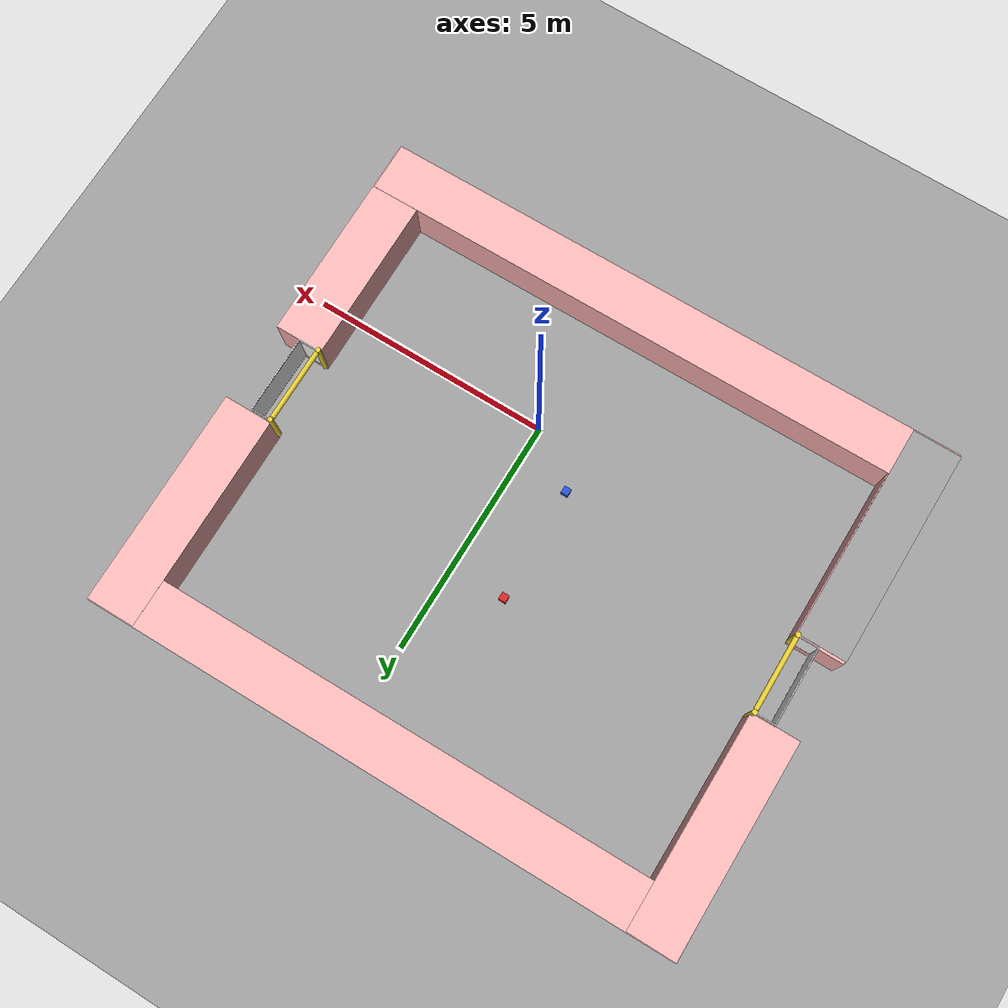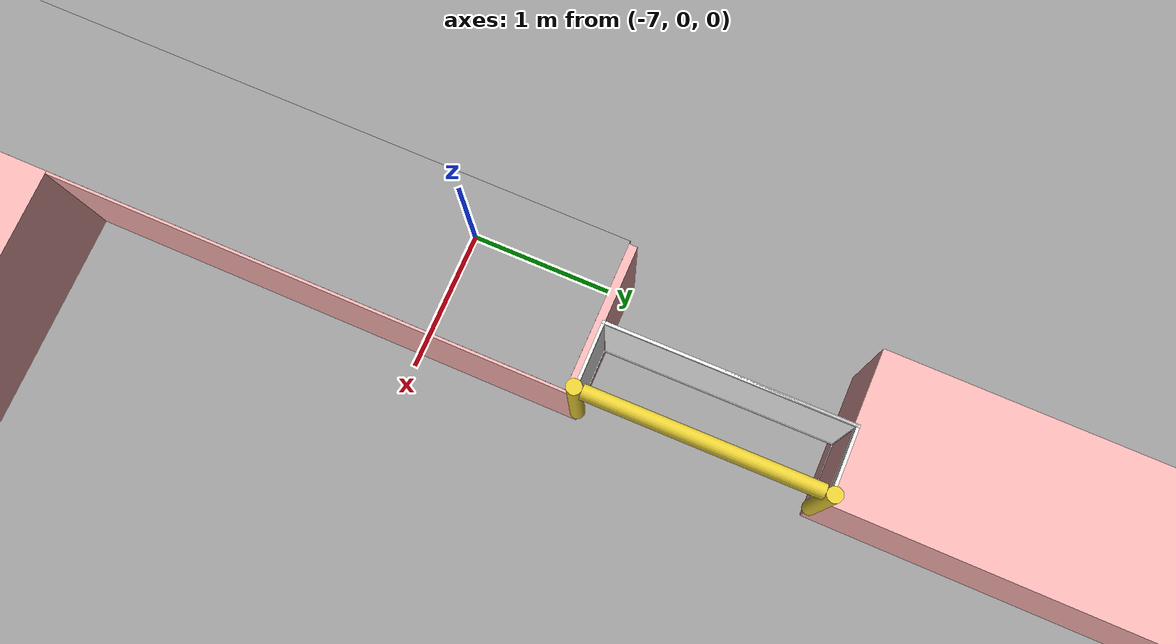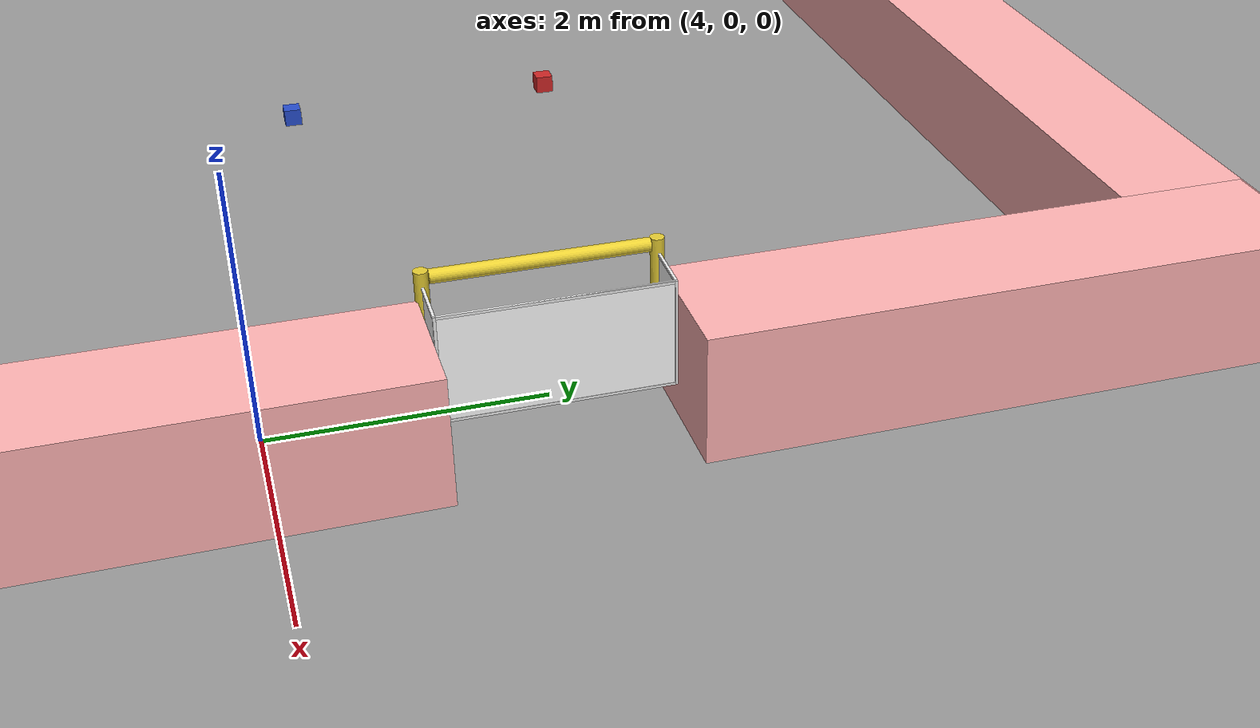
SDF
<sdf version="1.6">
 <world name="default">
  <light name="sun" type="directional">
   <pose>0 0 10 0 -0 0</pose>
   <diffuse>0.8 0.8 0.8 1</diffuse>
   <specular>0.1 0.1 0.1 1</specular>
   <attenuation>
    <range>1000</range>
    <constant>0.9</constant>
    <linear>0.01</linear>
    <quadratic>0.001</quadratic>
   </attenuation>
   <direction>-0.5 0.5 -1</direction>
  </light>
  <model name="ground_plane">
   <static>1</static>
   <link name="link">
    <collision name="collision">
     <geometry><plane><normal>0 0 1</normal><size>100 100</size></plane></geometry>
     <surface><friction><ode><mu>100</mu><mu2>50</mu2></ode></friction></surface>
    </collision>
    <visual name="visual">
     <cast_shadows>0</cast_shadows>
     <geometry><plane><normal>0 0 1</normal><size>100 100</size></plane></geometry>
     <material>
      <script><uri>file://media/materials/scripts/gazebo.material</uri><name>Gazebo/Grey</name></script>
     </material>
    </visual>
   </link>
  </model>
  <gravity>0 0 -9.8</gravity>
  <magnetic_field>6e-06 2.3e-05 -4.2e-05</magnetic_field>
  <atmosphere type="adiabatic"/>
  <physics name="default_physics" default="0" type="ode">
   <max_step_size>0.001</max_step_size>
   <real_time_factor>1</real_time_factor>
   <real_time_update_rate>1000</real_time_update_rate>
  </physics>
  <scene><ambient>0.4 0.4 0.4 1</ambient><background>0.7 0.7 0.7 1</background><shadows>1</shadows></scene>
  <spherical_coordinates>
   <surface_model>EARTH_WGS84</surface_model>
   <latitude_deg>0</latitude_deg>
   <longitude_deg>0</longitude_deg>
   <elevation>0</elevation>
   <heading_deg>0</heading_deg>
  </spherical_coordinates>
  <model name="unit_box_0_clone_0_0_clone_clone_0">
   <link name="link">
    <inertial>
     <mass>1</mass>
     <inertia>
      <ixx>0.166667</ixx>
      <ixy>0</ixy>
      <ixz>0</ixz>
      <iyy>0.166667</iyy>
      <iyz>0</iyz>
      <izz>0.166667</izz>
     </inertia>
    </inertial>
    <visual name="visual">
     <geometry><box><size>1 4.48154 1</size></box></geometry>
     <material>
      <script><name>Gazebo/Grey</name><uri>file://media/materials/scripts/gazebo.material</uri></script>
      <ambient>0.3 0.3 0.3 1</ambient>
      <diffuse>0.7 0.7 0.7 1</diffuse>
      <specular>0.01 0.01 0.01 1</specular>
      <emissive>0 0 0 1</emissive>
     </material>
    </visual>
    <collision name="collision">
     <geometry><box><size>1 4.48154 1</size></box></geometry>
     <surface>
      <friction>
       <ode><mu>1</mu><mu2>1</mu2><fdir1>0 0 0</fdir1><slip1>0</slip1><slip2>0</slip2></ode>
       <torsional>
        <coefficient>1</coefficient>
        <patch_radius>0</patch_radius>
        <surface_radius>0</surface_radius>
        <use_patch_radius>1</use_patch_radius>
        <ode><slip>0</slip></ode>
       </torsional>
      </friction>
      <bounce><restitution_coefficient>0</restitution_coefficient><threshold>1e+06</threshold></bounce>
      <contact>
       <collide_without_contact>0</collide_without_contact>
       <collide_without_contact_bitmask>1</collide_without_contact_bitmask>
       <collide_bitmask>1</collide_bitmask>
       <ode>
        <soft_cfm>0</soft_cfm>
        <soft_erp>0.2</soft_erp>
        <kp>1e+13</kp>
        <kd>1</kd>
        <max_vel>0.01</max_vel>
        <min_depth>0</min_depth>
       </ode>
       <bullet>
        <split_impulse>1</split_impulse>
        <split_impulse_penetration_threshold>-0.01</split_impulse_penetration_threshold>
        <soft_cfm>0</soft_cfm>
        <soft_erp>0.2</soft_erp>
        <kp>1e+13</kp>
        <kd>1</kd>
       </bullet>
      </contact>
     </surface>
    </collision>
   </link>
   <static>1</static>
   <pose>-6.60353 -1.13689 0.501162 -3.14102 -0 -3e-06</pose>
  </model>
  <light name="sun_0" type="directional">
   <pose>3.01034 -1.36988 10 0 -0 0</pose>
   <diffuse>0.8 0.8 0.8 1</diffuse>
   <specular>0.1 0.1 0.1 1</specular>
   <attenuation>
    <range>1000</range>
    <constant>0.9</constant>
    <linear>0.01</linear>
    <quadratic>0.001</quadratic>
   </attenuation>
   <direction>-0.5 0.5 -1</direction>
  </light>
  <model name="asphalt_plane_0_0">
   <link name="link">
    <inertial>
     <mass>1</mass>
     <inertia><ixx>1</ixx><ixy>0</ixy><ixz>0</ixz><iyy>1</iyy><iyz>0</iyz><izz>1</izz></inertia>
    </inertial>
    <visual name="visual">
     <cast_shadows>0</cast_shadows>
     <geometry><box><size>84.0868 136.428 0.1</size></box></geometry>
     <material>
      <script>
       <uri>model://asphalt_plane/materials/scripts</uri>
       <uri>model://asphalt_plane/materials/textures</uri>
       <name>Gazebo/Grey</name>
      </script>
      <ambient>0.1 0.1 0.1 1</ambient>
      <diffuse>0.1 0.1 0.1 1</diffuse>
      <specular>0.1 0.1 0.1 1</specular>
      <emissive>0 0 0 1</emissive>
      <shader type="vertex"><normal_map>__default__</normal_map></shader>
     </material>
    </visual>
    <collision name="collision">
     <geometry><box><size>84.0868 136.428 0.1</size></box></geometry>
     <surface>
      <friction>
       <ode><mu>1</mu><mu2>1</mu2><fdir1>0 0 0</fdir1><slip1>0</slip1><slip2>0</slip2></ode>
       <torsional>
        <coefficient>1</coefficient>
        <patch_radius>0</patch_radius>
        <surface_radius>0</surface_radius>
        <use_patch_radius>1</use_patch_radius>
        <ode><slip>0</slip></ode>
       </torsional>
      </friction>
      <bounce><restitution_coefficient>0</restitution_coefficient><threshold>1e+06</threshold></bounce>
      <contact>
       <collide_without_contact>0</collide_without_contact>
       <collide_without_contact_bitmask>1</collide_without_contact_bitmask>
       <collide_bitmask>1</collide_bitmask>
       <ode>
        <soft_cfm>0</soft_cfm>
        <soft_erp>0.2</soft_erp>
        <kp>1e+13</kp>
        <kd>1</kd>
        <max_vel>0.01</max_vel>
        <min_depth>0</min_depth>
       </ode>
       <bullet>
        <split_impulse>1</split_impulse>
        <split_impulse_penetration_threshold>-0.01</split_impulse_penetration_threshold>
        <soft_cfm>0</soft_cfm>
        <soft_erp>0.2</soft_erp>
        <kp>1e+13</kp>
        <kd>1</kd>
       </bullet>
      </contact>
     </surface>
    </collision>
   </link>
   <static>1</static>
   <pose>-0.546096 1.98012 0 0 -0 0</pose>
  </model>
  <model name="unit_box_0_clone_0_0_clone_clone_0_clone_clone_clone_0_0_clone_clone_0">
   <link name="link">
    <inertial>
     <mass>1</mass>
     <inertia>
      <ixx>0.166667</ixx>
      <ixy>0</ixy>
      <ixz>0</ixz>
      <iyy>0.166667</iyy>
      <iyz>0</iyz>
      <izz>0.166667</izz>
     </inertia>
    </inertial>
    <visual name="visual">
     <geometry><box><size>1 12.2515 1</size></box></geometry>
     <material>
      <script><name>Gazebo/Grey</name><uri>file://media/materials/scripts/gazebo.material</uri></script>
      <ambient>0.6 0.3 0.3 1</ambient>
      <diffuse>1 0.7 0.7 1</diffuse>
      <specular>0.31 0.01 0.01 1</specular>
      <emissive>0.7 0.7 0.7 1</emissive>
      <shader type="vertex"><normal_map>__default__</normal_map></shader>
     </material>
    </visual>
    <collision name="collision">
     <geometry><box><size>1 12.2515 1</size></box></geometry>
     <surface>
      <friction>
       <ode><mu>1</mu><mu2>1</mu2><fdir1>0 0 0</fdir1><slip1>0</slip1><slip2>0</slip2></ode>
       <torsional>
        <coefficient>1</coefficient>
        <patch_radius>0</patch_radius>
        <surface_radius>0</surface_radius>
        <use_patch_radius>1</use_patch_radius>
        <ode><slip>0</slip></ode>
       </torsional>
      </friction>
      <bounce><restitution_coefficient>0</restitution_coefficient><threshold>1e+06</threshold></bounce>
      <contact>
       <collide_without_contact>0</collide_without_contact>
       <collide_without_contact_bitmask>1</collide_without_contact_bitmask>
       <collide_bitmask>1</collide_bitmask>
       <ode>
        <soft_cfm>0</soft_cfm>
        <soft_erp>0.2</soft_erp>
        <kp>1e+13</kp>
        <kd>1</kd>
        <max_vel>0.01</max_vel>
        <min_depth>0</min_depth>
       </ode>
       <bullet>
        <split_impulse>1</split_impulse>
        <split_impulse_penetration_threshold>-0.01</split_impulse_penetration_threshold>
        <soft_cfm>0</soft_cfm>
        <soft_erp>0.2</soft_erp>
        <kp>1e+13</kp>
        <kd>1</kd>
       </bullet>
      </contact>
     </surface>
    </collision>
   </link>
   <static>1</static>
   <pose>-0.959818 6.7098 0.499628 3.14159 -0.000573 1.58078</pose>
  </model>
  <model name="unit_box_0_clone_0_0_clone_clone_0_clone_clone_clone_0_0_clone_0_0">
   <link name="link">
    <inertial>
     <mass>1</mass>
     <inertia>
      <ixx>0.166667</ixx>
      <ixy>0</ixy>
      <ixz>0</ixz>
      <iyy>0.166667</iyy>
      <iyz>0</iyz>
      <izz>0.166667</izz>
     </inertia>
    </inertial>
    <visual name="visual">
     <geometry><box><size>1 12.2515 1</size></box></geometry>
     <material>
      <script><name>Gazebo/Grey</name><uri>file://media/materials/scripts/gazebo.material</uri></script>
      <ambient>0.6 0.3 0.3 1</ambient>
      <diffuse>1 0.7 0.7 1</diffuse>
      <specular>0.31 0.01 0.01 1</specular>
      <emissive>0.7 0.7 0.7 1</emissive>
      <shader type="vertex"><normal_map>__default__</normal_map></shader>
     </material>
    </visual>
    <collision name="collision">
     <geometry><box><size>1 12.2515 1</size></box></geometry>
     <surface>
      <friction>
       <ode><mu>1</mu><mu2>1</mu2><fdir1>0 0 0</fdir1><slip1>0</slip1><slip2>0</slip2></ode>
       <torsional>
        <coefficient>1</coefficient>
        <patch_radius>0</patch_radius>
        <surface_radius>0</surface_radius>
        <use_patch_radius>1</use_patch_radius>
        <ode><slip>0</slip></ode>
       </torsional>
      </friction>
      <bounce><restitution_coefficient>0</restitution_coefficient><threshold>1e+06</threshold></bounce>
      <contact>
       <collide_without_contact>0</collide_without_contact>
       <collide_without_contact_bitmask>1</collide_without_contact_bitmask>
       <collide_bitmask>1</collide_bitmask>
       <ode>
        <soft_cfm>0</soft_cfm>
        <soft_erp>0.2</soft_erp>
        <kp>1e+13</kp>
        <kd>1</kd>
        <max_vel>0.01</max_vel>
        <min_depth>0</min_depth>
       </ode>
       <bullet>
        <split_impulse>1</split_impulse>
        <split_impulse_penetration_threshold>-0.01</split_impulse_penetration_threshold>
        <soft_cfm>0</soft_cfm>
        <soft_erp>0.2</soft_erp>
        <kp>1e+13</kp>
        <kd>1</kd>
       </bullet>
      </contact>
     </surface>
    </collision>
   </link>
   <static>1</static>
   <pose>-0.945242 -2.84309 0.499628 3.14159 -0.000573 1.58078</pose>
  </model>
  <model name="unit_box_0_clone_0_0_clone_clone_0_clone_clone_clone_0_clone_clone_0_clone_0_0">
   <link name="link">
    <inertial>
     <mass>1</mass>
     <inertia>
      <ixx>0.166667</ixx>
      <ixy>0</ixy>
      <ixz>0</ixz>
      <iyy>0.166667</iyy>
      <iyz>0</iyz>
      <izz>0.166667</izz>
     </inertia>
    </inertial>
    <visual name="visual">
     <geometry><box><size>1 4.38827 1</size></box></geometry>
     <material>
      <script><name>Gazebo/Grey</name><uri>file://media/materials/scripts/gazebo.material</uri></script>
      <ambient>0.6 0.3 0.3 1</ambient>
      <diffuse>1 0.7 0.7 1</diffuse>
      <specular>0.31 0.01 0.01 1</specular>
      <emissive>0.7 0.7 0.7 1</emissive>
      <shader type="vertex"><normal_map>__default__</normal_map></shader>
     </material>
    </visual>
    <collision name="collision">
     <geometry><box><size>1 4.38827 1</size></box></geometry>
     <surface>
      <friction>
       <ode><mu>1</mu><mu2>1</mu2><fdir1>0 0 0</fdir1><slip1>0</slip1><slip2>0</slip2></ode>
       <torsional>
        <coefficient>1</coefficient>
        <patch_radius>0</patch_radius>
        <surface_radius>0</surface_radius>
        <use_patch_radius>1</use_patch_radius>
        <ode><slip>0</slip></ode>
       </torsional>
      </friction>
      <bounce><restitution_coefficient>0</restitution_coefficient><threshold>1e+06</threshold></bounce>
      <contact>
       <collide_without_contact>0</collide_without_contact>
       <collide_without_contact_bitmask>1</collide_without_contact_bitmask>
       <collide_bitmask>1</collide_bitmask>
       <ode>
        <soft_cfm>0</soft_cfm>
        <soft_erp>0.2</soft_erp>
        <kp>1e+13</kp>
        <kd>1</kd>
        <max_vel>0.01</max_vel>
        <min_depth>0</min_depth>
       </ode>
       <bullet>
        <split_impulse>1</split_impulse>
        <split_impulse_penetration_threshold>-0.01</split_impulse_penetration_threshold>
        <soft_cfm>0</soft_cfm>
        <soft_erp>0.2</soft_erp>
        <kp>1e+13</kp>
        <kd>1</kd>
       </bullet>
      </contact>
     </surface>
    </collision>
   </link>
   <static>1</static>
   <pose>4.68681 -1.07681 0.49976 -3.14102 -0 0.006143</pose>
  </model>
  <model name="unit_box_0_clone_0_0_clone_clone_0_clone_clone_clone_0_clone_clone_0_0_0">
   <link name="link">
    <inertial>
     <mass>1</mass>
     <inertia>
      <ixx>0.166667</ixx>
      <ixy>0</ixy>
      <ixz>0</ixz>
      <iyy>0.166667</iyy>
      <iyz>0</iyz>
      <izz>0.166667</izz>
     </inertia>
    </inertial>
    <visual name="visual">
     <geometry><box><size>1 4.48154 1</size></box></geometry>
     <material>
      <script><name>Gazebo/Grey</name><uri>file://media/materials/scripts/gazebo.material</uri></script>
      <ambient>0.6 0.3 0.3 1</ambient>
      <diffuse>1 0.7 0.7 1</diffuse>
      <specular>0.31 0.01 0.01 1</specular>
      <emissive>0.7 0.7 0.7 1</emissive>
      <shader type="vertex"><normal_map>__default__</normal_map></shader>
     </material>
    </visual>
    <collision name="collision">
     <geometry><box><size>1 4.48154 1</size></box></geometry>
     <surface>
      <friction>
       <ode><mu>1</mu><mu2>1</mu2><fdir1>0 0 0</fdir1><slip1>0</slip1><slip2>0</slip2></ode>
       <torsional>
        <coefficient>1</coefficient>
        <patch_radius>0</patch_radius>
        <surface_radius>0</surface_radius>
        <use_patch_radius>1</use_patch_radius>
        <ode><slip>0</slip></ode>
       </torsional>
      </friction>
      <bounce><restitution_coefficient>0</restitution_coefficient><threshold>1e+06</threshold></bounce>
      <contact>
       <collide_without_contact>0</collide_without_contact>
       <collide_without_contact_bitmask>1</collide_without_contact_bitmask>
       <collide_bitmask>1</collide_bitmask>
       <ode>
        <soft_cfm>0</soft_cfm>
        <soft_erp>0.2</soft_erp>
        <kp>1e+13</kp>
        <kd>1</kd>
        <max_vel>0.01</max_vel>
        <min_depth>0</min_depth>
       </ode>
       <bullet>
        <split_impulse>1</split_impulse>
        <split_impulse_penetration_threshold>-0.01</split_impulse_penetration_threshold>
        <soft_cfm>0</soft_cfm>
        <soft_erp>0.2</soft_erp>
        <kp>1e+13</kp>
        <kd>1</kd>
       </bullet>
      </contact>
     </surface>
    </collision>
   </link>
   <static>1</static>
   <pose>4.68506 5.01169 0.49975 -3.14102 -0 0.006143</pose>
  </model>
  <model name="unit_box_0_clone_0_0_0_0">
   <link name="link">
    <inertial>
     <mass>1</mass>
     <inertia>
      <ixx>0.166667</ixx>
      <ixy>0</ixy>
      <ixz>0</ixz>
      <iyy>0.166667</iyy>
      <iyz>0</iyz>
      <izz>0.166667</izz>
     </inertia>
    </inertial>
    <visual name="visual">
     <geometry><box><size>1 4.48154 1</size></box></geometry>
     <material>
      <script><name>Gazebo/Grey</name><uri>file://media/materials/scripts/gazebo.material</uri></script>
      <ambient>0.6 0.3 0.3 1</ambient>
      <diffuse>1 0.7 0.7 1</diffuse>
      <specular>0.31 0.01 0.01 1</specular>
      <emissive>0.7 0.7 0.7 1</emissive>
      <shader type="vertex"><normal_map>__default__</normal_map></shader>
     </material>
    </visual>
    <collision name="collision">
     <geometry><box><size>1 4.48154 1</size></box></geometry>
     <surface>
      <friction>
       <ode><mu>1</mu><mu2>1</mu2><fdir1>0 0 0</fdir1><slip1>0</slip1><slip2>0</slip2></ode>
       <torsional>
        <coefficient>1</coefficient>
        <patch_radius>0</patch_radius>
        <surface_radius>0</surface_radius>
        <use_patch_radius>1</use_patch_radius>
        <ode><slip>0</slip></ode>
       </torsional>
      </friction>
      <bounce><restitution_coefficient>0</restitution_coefficient><threshold>1e+06</threshold></bounce>
      <contact>
       <collide_without_contact>0</collide_without_contact>
       <collide_without_contact_bitmask>1</collide_without_contact_bitmask>
       <collide_bitmask>1</collide_bitmask>
       <ode>
        <soft_cfm>0</soft_cfm>
        <soft_erp>0.2</soft_erp>
        <kp>1e+13</kp>
        <kd>1</kd>
        <max_vel>0.01</max_vel>
        <min_depth>0</min_depth>
       </ode>
       <bullet>
        <split_impulse>1</split_impulse>
        <split_impulse_penetration_threshold>-0.01</split_impulse_penetration_threshold>
        <soft_cfm>0</soft_cfm>
        <soft_erp>0.2</soft_erp>
        <kp>1e+13</kp>
        <kd>1</kd>
       </bullet>
      </contact>
     </surface>
    </collision>
   </link>
   <static>1</static>
   <pose>-6.5853 -1.08093 0.49872 -3.14102 -0 -3e-06</pose>
  </model>
  <model name="unit_box_0_clone_0_0_clone_0_0">
   <link name="link">
    <inertial>
     <mass>1</mass>
     <inertia>
      <ixx>0.166667</ixx>
      <ixy>0</ixy>
      <ixz>0</ixz>
      <iyy>0.166667</iyy>
      <iyz>0</iyz>
      <izz>0.166667</izz>
     </inertia>
    </inertial>
    <visual name="visual">
     <geometry><box><size>1 4.38308 1</size></box></geometry>
     <material>
      <script><name>Gazebo/Grey</name><uri>file://media/materials/scripts/gazebo.material</uri></script>
      <ambient>0.6 0.3 0.3 1</ambient>
      <diffuse>1 0.7 0.7 1</diffuse>
      <specular>0.31 0.01 0.01 1</specular>
      <emissive>0.7 0.7 0.7 1</emissive>
      <shader type="vertex"><normal_map>__default__</normal_map></shader>
     </material>
    </visual>
    <collision name="collision">
     <geometry><box><size>1 4.38308 1</size></box></geometry>
     <surface>
      <friction>
       <ode><mu>1</mu><mu2>1</mu2><fdir1>0 0 0</fdir1><slip1>0</slip1><slip2>0</slip2></ode>
       <torsional>
        <coefficient>1</coefficient>
        <patch_radius>0</patch_radius>
        <surface_radius>0</surface_radius>
        <use_patch_radius>1</use_patch_radius>
        <ode><slip>0</slip></ode>
       </torsional>
      </friction>
      <bounce><restitution_coefficient>0</restitution_coefficient><threshold>1e+06</threshold></bounce>
      <contact>
       <collide_without_contact>0</collide_without_contact>
       <collide_without_contact_bitmask>1</collide_without_contact_bitmask>
       <collide_bitmask>1</collide_bitmask>
       <ode>
        <soft_cfm>0</soft_cfm>
        <soft_erp>0.2</soft_erp>
        <kp>1e+13</kp>
        <kd>1</kd>
        <max_vel>0.01</max_vel>
        <min_depth>0</min_depth>
       </ode>
       <bullet>
        <split_impulse>1</split_impulse>
        <split_impulse_penetration_threshold>-0.01</split_impulse_penetration_threshold>
        <soft_cfm>0</soft_cfm>
        <soft_erp>0.2</soft_erp>
        <kp>1e+13</kp>
        <kd>1</kd>
       </bullet>
      </contact>
     </surface>
    </collision>
   </link>
   <static>1</static>
   <pose>-6.58164 4.95131 0.498874 -3.14102 -0 -3e-06</pose>
  </model>
  <model name="RoboCup_2014_SPL_Goal_clone_0">
   <link name="left_post">
    <pose>-0 0.8 0.45 0 -0 0</pose>
    <visual name="visual">
     <geometry><cylinder><radius>0.05</radius><length>0.9</length></cylinder></geometry>
     <material>
      <script><uri>file://media/materials/scripts/gazebo.material</uri><name>Gazebo/ZincYellow</name></script>
      <ambient>0.9725 0.9529 0.2078 1</ambient>
      <diffuse>0.9725 0.9529 0.2078 1</diffuse>
      <specular>0.9725 0.9529 0.2078 1</specular>
      <emissive>0 0 0 1</emissive>
     </material>
    </visual>
    <collision name="collision">
     <geometry><cylinder><radius>0.05</radius><length>0.9</length></cylinder></geometry>
     <surface>
      <friction>
       <ode><mu>1</mu><mu2>1</mu2><fdir1>0 0 0</fdir1><slip1>0</slip1><slip2>0</slip2></ode>
       <torsional>
        <coefficient>1</coefficient>
        <patch_radius>0</patch_radius>
        <surface_radius>0</surface_radius>
        <use_patch_radius>1</use_patch_radius>
        <ode><slip>0</slip></ode>
       </torsional>
      </friction>
      <bounce><restitution_coefficient>0</restitution_coefficient><threshold>1e+06</threshold></bounce>
      <contact>
       <collide_without_contact>0</collide_without_contact>
       <collide_without_contact_bitmask>1</collide_without_contact_bitmask>
       <collide_bitmask>1</collide_bitmask>
       <ode>
        <soft_cfm>0</soft_cfm>
        <soft_erp>0.2</soft_erp>
        <kp>1e+13</kp>
        <kd>1</kd>
        <max_vel>0.01</max_vel>
        <min_depth>0</min_depth>
       </ode>
       <bullet>
        <split_impulse>1</split_impulse>
        <split_impulse_penetration_threshold>-0.01</split_impulse_penetration_threshold>
        <soft_cfm>0</soft_cfm>
        <soft_erp>0.2</soft_erp>
        <kp>1e+13</kp>
        <kd>1</kd>
       </bullet>
      </contact>
     </surface>
    </collision>
   </link>
   <link name="center_net">
    <pose>0.44 -0 0.4 0 -0 0</pose>
    <inertial>
     <mass>1</mass>
     <inertia><ixx>1</ixx><ixy>0</ixy><ixz>0</ixz><iyy>1</iyy><iyz>0</iyz><izz>1</izz></inertia>
    </inertial>
    <visual name="visual">
     <geometry><box><size>0.01 1.6 0.8</size></box></geometry>
     <material>
      <script>
       <uri>model://robocup09_spl_field/materials/scripts/</uri>
       <uri>model://robocup09_spl_field/materials/textures/</uri>
       <name>RoboCup/Net</name>
      </script>
      <ambient>1 1 1 1</ambient>
      <diffuse>1 1 1 1</diffuse>
      <specular>0 0 0 1</specular>
      <emissive>1 1 0 1</emissive>
      <shader type="vertex"><normal_map>__default__</normal_map></shader>
     </material>
    </visual>
    <collision name="collision">
     <geometry><box><size>0.01 1.6 0.8</size></box></geometry>
     <surface>
      <friction>
       <ode><mu>1</mu><mu2>1</mu2><fdir1>0 0 0</fdir1><slip1>0</slip1><slip2>0</slip2></ode>
       <torsional>
        <coefficient>1</coefficient>
        <patch_radius>0</patch_radius>
        <surface_radius>0</surface_radius>
        <use_patch_radius>1</use_patch_radius>
        <ode><slip>0</slip></ode>
       </torsional>
      </friction>
      <bounce><restitution_coefficient>0</restitution_coefficient><threshold>1e+06</threshold></bounce>
      <contact>
       <collide_without_contact>0</collide_without_contact>
       <collide_without_contact_bitmask>1</collide_without_contact_bitmask>
       <collide_bitmask>1</collide_bitmask>
       <ode>
        <soft_cfm>0</soft_cfm>
        <soft_erp>0.2</soft_erp>
        <kp>1e+13</kp>
        <kd>1</kd>
        <max_vel>0.01</max_vel>
        <min_depth>0</min_depth>
       </ode>
       <bullet>
        <split_impulse>1</split_impulse>
        <split_impulse_penetration_threshold>-0.01</split_impulse_penetration_threshold>
        <soft_cfm>0</soft_cfm>
        <soft_erp>0.2</soft_erp>
        <kp>1e+13</kp>
        <kd>1</kd>
       </bullet>
      </contact>
     </surface>
    </collision>
   </link>
   <link name="center_support_horiz_lower">
    <pose>0.44 -0 0.01 3.14158 1.57079 3.14158</pose>
    <visual name="visual">
     <geometry><box><size>0.02 1.58 0.02</size></box></geometry>
     <material>
      <script><uri>file://media/materials/scripts/gazebo.material</uri><name>Gazebo/White</name></script>
      <ambient>1 1 1 1</ambient>
      <diffuse>1 1 1 1</diffuse>
      <specular>0 0 0 1</specular>
      <emissive>0 0 0 1</emissive>
     </material>
    </visual>
    <collision name="collision">
     <geometry><box><size>0.02 1.58 0.02</size></box></geometry>
     <surface>
      <friction>
       <ode><mu>1</mu><mu2>1</mu2><fdir1>0 0 0</fdir1><slip1>0</slip1><slip2>0</slip2></ode>
       <torsional>
        <coefficient>1</coefficient>
        <patch_radius>0</patch_radius>
        <surface_radius>0</surface_radius>
        <use_patch_radius>1</use_patch_radius>
        <ode><slip>0</slip></ode>
       </torsional>
      </friction>
      <bounce><restitution_coefficient>0</restitution_coefficient><threshold>1e+06</threshold></bounce>
      <contact>
       <collide_without_contact>0</collide_without_contact>
       <collide_without_contact_bitmask>1</collide_without_contact_bitmask>
       <collide_bitmask>1</collide_bitmask>
       <ode>
        <soft_cfm>0</soft_cfm>
        <soft_erp>0.2</soft_erp>
        <kp>1e+13</kp>
        <kd>1</kd>
        <max_vel>0.01</max_vel>
        <min_depth>0</min_depth>
       </ode>
       <bullet>
        <split_impulse>1</split_impulse>
        <split_impulse_penetration_threshold>-0.01</split_impulse_penetration_threshold>
        <soft_cfm>0</soft_cfm>
        <soft_erp>0.2</soft_erp>
        <kp>1e+13</kp>
        <kd>1</kd>
       </bullet>
      </contact>
     </surface>
    </collision>
   </link>
   <link name="center_support_horiz_upper">
    <pose>0.44 -0 0.79 3.14158 1.57079 3.14158</pose>
    <visual name="visual">
     <geometry><box><size>0.02 1.58 0.02</size></box></geometry>
     <material>
      <script><uri>file://media/materials/scripts/gazebo.material</uri><name>Gazebo/White</name></script>
      <ambient>1 1 1 1</ambient>
      <diffuse>1 1 1 1</diffuse>
      <specular>0 0 0 1</specular>
      <emissive>0 0 0 1</emissive>
     </material>
    </visual>
    <collision name="collision">
     <geometry><box><size>0.02 1.58 0.02</size></box></geometry>
     <surface>
      <friction>
       <ode><mu>1</mu><mu2>1</mu2><fdir1>0 0 0</fdir1><slip1>0</slip1><slip2>0</slip2></ode>
       <torsional>
        <coefficient>1</coefficient>
        <patch_radius>0</patch_radius>
        <surface_radius>0</surface_radius>
        <use_patch_radius>1</use_patch_radius>
        <ode><slip>0</slip></ode>
       </torsional>
      </friction>
      <bounce><restitution_coefficient>0</restitution_coefficient><threshold>1e+06</threshold></bounce>
      <contact>
       <collide_without_contact>0</collide_without_contact>
       <collide_without_contact_bitmask>1</collide_without_contact_bitmask>
       <collide_bitmask>1</collide_bitmask>
       <ode>
        <soft_cfm>0</soft_cfm>
        <soft_erp>0.2</soft_erp>
        <kp>1e+13</kp>
        <kd>1</kd>
        <max_vel>0.01</max_vel>
        <min_depth>0</min_depth>
       </ode>
       <bullet>
        <split_impulse>1</split_impulse>
        <split_impulse_penetration_threshold>-0.01</split_impulse_penetration_threshold>
        <soft_cfm>0</soft_cfm>
        <soft_erp>0.2</soft_erp>
        <kp>1e+13</kp>
        <kd>1</kd>
       </bullet>
      </contact>
     </surface>
    </collision>
   </link>
   <link name="crossbar">
    <pose>0 0 0.85 1.57011 1.57 0.000106</pose>
    <visual name="visual">
     <geometry><cylinder><radius>0.05</radius><length>1.5</length></cylinder></geometry>
     <material>
      <script><uri>file://media/materials/scripts/gazebo.material</uri><name>Gazebo/ZincYellow</name></script>
      <ambient>0.9725 0.9529 0.2078 1</ambient>
      <diffuse>0.9725 0.9529 0.2078 1</diffuse>
      <specular>0.9725 0.9529 0.2078 1</specular>
      <emissive>0 0 0 1</emissive>
     </material>
    </visual>
    <collision name="collision">
     <geometry><cylinder><radius>0.05</radius><length>1.5</length></cylinder></geometry>
     <surface>
      <friction>
       <ode><mu>1</mu><mu2>1</mu2><fdir1>0 0 0</fdir1><slip1>0</slip1><slip2>0</slip2></ode>
       <torsional>
        <coefficient>1</coefficient>
        <patch_radius>0</patch_radius>
        <surface_radius>0</surface_radius>
        <use_patch_radius>1</use_patch_radius>
        <ode><slip>0</slip></ode>
       </torsional>
      </friction>
      <bounce><restitution_coefficient>0</restitution_coefficient><threshold>1e+06</threshold></bounce>
      <contact>
       <collide_without_contact>0</collide_without_contact>
       <collide_without_contact_bitmask>1</collide_without_contact_bitmask>
       <collide_bitmask>1</collide_bitmask>
       <ode>
        <soft_cfm>0</soft_cfm>
        <soft_erp>0.2</soft_erp>
        <kp>1e+13</kp>
        <kd>1</kd>
        <max_vel>0.01</max_vel>
        <min_depth>0</min_depth>
       </ode>
       <bullet>
        <split_impulse>1</split_impulse>
        <split_impulse_penetration_threshold>-0.01</split_impulse_penetration_threshold>
        <soft_cfm>0</soft_cfm>
        <soft_erp>0.2</soft_erp>
        <kp>1e+13</kp>
        <kd>1</kd>
       </bullet>
      </contact>
     </surface>
    </collision>
   </link>
   <link name="left_net">
    <pose>0.24 0.8 0.4 0 -0 0</pose>
    <visual name="visual">
     <geometry><box><size>0.38 0.01 0.76</size></box></geometry>
     <material>
      <script>
       <uri>model://robocup09_spl_field/materials/scripts/</uri>
       <uri>model://robocup09_spl_field/materials/textures/</uri>
       <name>RoboCup/Net</name>
      </script>
      <ambient>1 1 1 1</ambient>
      <diffuse>1 1 1 1</diffuse>
      <specular>0 0 0 1</specular>
      <emissive>0 0 0 1</emissive>
     </material>
    </visual>
    <collision name="collision">
     <geometry><box><size>0.38 0.01 0.76</size></box></geometry>
     <surface>
      <friction>
       <ode><mu>1</mu><mu2>1</mu2><fdir1>0 0 0</fdir1><slip1>0</slip1><slip2>0</slip2></ode>
       <torsional>
        <coefficient>1</coefficient>
        <patch_radius>0</patch_radius>
        <surface_radius>0</surface_radius>
        <use_patch_radius>1</use_patch_radius>
        <ode><slip>0</slip></ode>
       </torsional>
      </friction>
      <bounce><restitution_coefficient>0</restitution_coefficient><threshold>1e+06</threshold></bounce>
      <contact>
       <collide_without_contact>0</collide_without_contact>
       <collide_without_contact_bitmask>1</collide_without_contact_bitmask>
       <collide_bitmask>1</collide_bitmask>
       <ode>
        <soft_cfm>0</soft_cfm>
        <soft_erp>0.2</soft_erp>
        <kp>1e+13</kp>
        <kd>1</kd>
        <max_vel>0.01</max_vel>
        <min_depth>0</min_depth>
       </ode>
       <bullet>
        <split_impulse>1</split_impulse>
        <split_impulse_penetration_threshold>-0.01</split_impulse_penetration_threshold>
        <soft_cfm>0</soft_cfm>
        <soft_erp>0.2</soft_erp>
        <kp>1e+13</kp>
        <kd>1</kd>
       </bullet>
      </contact>
     </surface>
    </collision>
   </link>
   <link name="left_support_horiz_lower">
    <pose>0.24 0.8 0.01 0 -0 0</pose>
    <visual name="visual">
     <geometry><box><size>0.38 0.02 0.02</size></box></geometry>
     <material>
      <script><uri>file://media/materials/scripts/gazebo.material</uri><name>Gazebo/White</name></script>
      <ambient>1 1 1 1</ambient>
      <diffuse>1 1 1 1</diffuse>
      <specular>0 0 0 1</specular>
      <emissive>0 0 0 1</emissive>
     </material>
    </visual>
    <collision name="collision">
     <geometry><box><size>0.38 0.02 0.02</size></box></geometry>
     <surface>
      <friction>
       <ode><mu>1</mu><mu2>1</mu2><fdir1>0 0 0</fdir1><slip1>0</slip1><slip2>0</slip2></ode>
       <torsional>
        <coefficient>1</coefficient>
        <patch_radius>0</patch_radius>
        <surface_radius>0</surface_radius>
        <use_patch_radius>1</use_patch_radius>
        <ode><slip>0</slip></ode>
       </torsional>
      </friction>
      <bounce><restitution_coefficient>0</restitution_coefficient><threshold>1e+06</threshold></bounce>
      <contact>
       <collide_without_contact>0</collide_without_contact>
       <collide_without_contact_bitmask>1</collide_without_contact_bitmask>
       <collide_bitmask>1</collide_bitmask>
       <ode>
        <soft_cfm>0</soft_cfm>
        <soft_erp>0.2</soft_erp>
        <kp>1e+13</kp>
        <kd>1</kd>
        <max_vel>0.01</max_vel>
        <min_depth>0</min_depth>
       </ode>
       <bullet>
        <split_impulse>1</split_impulse>
        <split_impulse_penetration_threshold>-0.01</split_impulse_penetration_threshold>
        <soft_cfm>0</soft_cfm>
        <soft_erp>0.2</soft_erp>
        <kp>1e+13</kp>
        <kd>1</kd>
       </bullet>
      </contact>
     </surface>
    </collision>
   </link>
   <link name="left_support_horiz_upper">
    <pose>0.24 0.8 0.79 0 -0 0</pose>
    <visual name="visual">
     <geometry><box><size>0.38 0.02 0.02</size></box></geometry>
     <material>
      <script><uri>file://media/materials/scripts/gazebo.material</uri><name>Gazebo/White</name></script>
      <ambient>1 1 1 1</ambient>
      <diffuse>1 1 1 1</diffuse>
      <specular>0 0 0 1</specular>
      <emissive>0 0 0 1</emissive>
     </material>
    </visual>
    <collision name="collision">
     <geometry><box><size>0.38 0.02 0.02</size></box></geometry>
     <surface>
      <friction>
       <ode><mu>1</mu><mu2>1</mu2><fdir1>0 0 0</fdir1><slip1>0</slip1><slip2>0</slip2></ode>
       <torsional>
        <coefficient>1</coefficient>
        <patch_radius>0</patch_radius>
        <surface_radius>0</surface_radius>
        <use_patch_radius>1</use_patch_radius>
        <ode><slip>0</slip></ode>
       </torsional>
      </friction>
      <bounce><restitution_coefficient>0</restitution_coefficient><threshold>1e+06</threshold></bounce>
      <contact>
       <collide_without_contact>0</collide_without_contact>
       <collide_without_contact_bitmask>1</collide_without_contact_bitmask>
       <collide_bitmask>1</collide_bitmask>
       <ode>
        <soft_cfm>0</soft_cfm>
        <soft_erp>0.2</soft_erp>
        <kp>1e+13</kp>
        <kd>1</kd>
        <max_vel>0.01</max_vel>
        <min_depth>0</min_depth>
       </ode>
       <bullet>
        <split_impulse>1</split_impulse>
        <split_impulse_penetration_threshold>-0.01</split_impulse_penetration_threshold>
        <soft_cfm>0</soft_cfm>
        <soft_erp>0.2</soft_erp>
        <kp>1e+13</kp>
        <kd>1</kd>
       </bullet>
      </contact>
     </surface>
    </collision>
   </link>
   <link name="left_support_vertical">
    <pose>0.44 0.8 0.4 3.14158 1.57079 3.14158</pose>
    <visual name="visual">
     <geometry><box><size>0.8 0.02 0.02</size></box></geometry>
     <material>
      <script><uri>file://media/materials/scripts/gazebo.material</uri><name>Gazebo/White</name></script>
      <ambient>1 1 1 1</ambient>
      <diffuse>1 1 1 1</diffuse>
      <specular>0 0 0 1</specular>
      <emissive>0 0 0 1</emissive>
     </material>
    </visual>
    <collision name="collision">
     <geometry><box><size>0.8 0.02 0.02</size></box></geometry>
     <surface>
      <friction>
       <ode><mu>1</mu><mu2>1</mu2><fdir1>0 0 0</fdir1><slip1>0</slip1><slip2>0</slip2></ode>
       <torsional>
        <coefficient>1</coefficient>
        <patch_radius>0</patch_radius>
        <surface_radius>0</surface_radius>
        <use_patch_radius>1</use_patch_radius>
        <ode><slip>0</slip></ode>
       </torsional>
      </friction>
      <bounce><restitution_coefficient>0</restitution_coefficient><threshold>1e+06</threshold></bounce>
      <contact>
       <collide_without_contact>0</collide_without_contact>
       <collide_without_contact_bitmask>1</collide_without_contact_bitmask>
       <collide_bitmask>1</collide_bitmask>
       <ode>
        <soft_cfm>0</soft_cfm>
        <soft_erp>0.2</soft_erp>
        <kp>1e+13</kp>
        <kd>1</kd>
        <max_vel>0.01</max_vel>
        <min_depth>0</min_depth>
       </ode>
       <bullet>
        <split_impulse>1</split_impulse>
        <split_impulse_penetration_threshold>-0.01</split_impulse_penetration_threshold>
        <soft_cfm>0</soft_cfm>
        <soft_erp>0.2</soft_erp>
        <kp>1e+13</kp>
        <kd>1</kd>
       </bullet>
      </contact>
     </surface>
    </collision>
   </link>
   <link name="right_net">
    <pose>0.24 -0.8 0.4 0 -0 0</pose>
    <visual name="visual">
     <geometry><box><size>0.38 0.01 0.76</size></box></geometry>
     <material>
      <script>
       <uri>model://robocup09_spl_field/materials/scripts/</uri>
       <uri>model://robocup09_spl_field/materials/textures/</uri>
       <name>RoboCup/Net</name>
      </script>
      <ambient>1 1 1 1</ambient>
      <diffuse>1 1 1 1</diffuse>
      <specular>0 0 0 1</specular>
      <emissive>0 0 0 1</emissive>
     </material>
    </visual>
    <collision name="collision">
     <geometry><box><size>0.38 0.01 0.76</size></box></geometry>
     <surface>
      <friction>
       <ode><mu>1</mu><mu2>1</mu2><fdir1>0 0 0</fdir1><slip1>0</slip1><slip2>0</slip2></ode>
       <torsional>
        <coefficient>1</coefficient>
        <patch_radius>0</patch_radius>
        <surface_radius>0</surface_radius>
        <use_patch_radius>1</use_patch_radius>
        <ode><slip>0</slip></ode>
       </torsional>
      </friction>
      <bounce><restitution_coefficient>0</restitution_coefficient><threshold>1e+06</threshold></bounce>
      <contact>
       <collide_without_contact>0</collide_without_contact>
       <collide_without_contact_bitmask>1</collide_without_contact_bitmask>
       <collide_bitmask>1</collide_bitmask>
       <ode>
        <soft_cfm>0</soft_cfm>
        <soft_erp>0.2</soft_erp>
        <kp>1e+13</kp>
        <kd>1</kd>
        <max_vel>0.01</max_vel>
        <min_depth>0</min_depth>
       </ode>
       <bullet>
        <split_impulse>1</split_impulse>
        <split_impulse_penetration_threshold>-0.01</split_impulse_penetration_threshold>
        <soft_cfm>0</soft_cfm>
        <soft_erp>0.2</soft_erp>
        <kp>1e+13</kp>
        <kd>1</kd>
       </bullet>
      </contact>
     </surface>
    </collision>
   </link>
   <link name="right_post">
    <pose>0 -0.8 0.45 0 -0 0</pose>
    <visual name="visual">
     <geometry><cylinder><radius>0.05</radius><length>0.9</length></cylinder></geometry>
     <material>
      <script><uri>file://media/materials/scripts/gazebo.material</uri><name>Gazebo/ZincYellow</name></script>
      <ambient>0.9725 0.9529 0.2078 1</ambient>
      <diffuse>0.9725 0.9529 0.2078 1</diffuse>
      <specular>0.9725 0.9529 0.2078 1</specular>
      <emissive>0 0 0 1</emissive>
     </material>
    </visual>
    <collision name="collision">
     <geometry><cylinder><radius>0.05</radius><length>0.9</length></cylinder></geometry>
     <surface>
      <friction>
       <ode><mu>1</mu><mu2>1</mu2><fdir1>0 0 0</fdir1><slip1>0</slip1><slip2>0</slip2></ode>
       <torsional>
        <coefficient>1</coefficient>
        <patch_radius>0</patch_radius>
        <surface_radius>0</surface_radius>
        <use_patch_radius>1</use_patch_radius>
        <ode><slip>0</slip></ode>
       </torsional>
      </friction>
      <bounce><restitution_coefficient>0</restitution_coefficient><threshold>1e+06</threshold></bounce>
      <contact>
       <collide_without_contact>0</collide_without_contact>
       <collide_without_contact_bitmask>1</collide_without_contact_bitmask>
       <collide_bitmask>1</collide_bitmask>
       <ode>
        <soft_cfm>0</soft_cfm>
        <soft_erp>0.2</soft_erp>
        <kp>1e+13</kp>
        <kd>1</kd>
        <max_vel>0.01</max_vel>
        <min_depth>0</min_depth>
       </ode>
       <bullet>
        <split_impulse>1</split_impulse>
        <split_impulse_penetration_threshold>-0.01</split_impulse_penetration_threshold>
        <soft_cfm>0</soft_cfm>
        <soft_erp>0.2</soft_erp>
        <kp>1e+13</kp>
        <kd>1</kd>
       </bullet>
      </contact>
     </surface>
    </collision>
   </link>
   <link name="right_support_horiz_lower">
    <pose>0.24 -0.8 0.01 0 -0 0</pose>
    <visual name="visual">
     <geometry><box><size>0.38 0.02 0.02</size></box></geometry>
     <material>
      <script><uri>file://media/materials/scripts/gazebo.material</uri><name>Gazebo/White</name></script>
      <ambient>1 1 1 1</ambient>
      <diffuse>1 1 1 1</diffuse>
      <specular>0 0 0 1</specular>
      <emissive>0 0 0 1</emissive>
     </material>
    </visual>
    <collision name="collision">
     <geometry><box><size>0.38 0.02 0.02</size></box></geometry>
     <surface>
      <friction>
       <ode><mu>1</mu><mu2>1</mu2><fdir1>0 0 0</fdir1><slip1>0</slip1><slip2>0</slip2></ode>
       <torsional>
        <coefficient>1</coefficient>
        <patch_radius>0</patch_radius>
        <surface_radius>0</surface_radius>
        <use_patch_radius>1</use_patch_radius>
        <ode><slip>0</slip></ode>
       </torsional>
      </friction>
      <bounce><restitution_coefficient>0</restitution_coefficient><threshold>1e+06</threshold></bounce>
      <contact>
       <collide_without_contact>0</collide_without_contact>
       <collide_without_contact_bitmask>1</collide_without_contact_bitmask>
       <collide_bitmask>1</collide_bitmask>
       <ode>
        <soft_cfm>0</soft_cfm>
        <soft_erp>0.2</soft_erp>
        <kp>1e+13</kp>
        <kd>1</kd>
        <max_vel>0.01</max_vel>
        <min_depth>0</min_depth>
       </ode>
       <bullet>
        <split_impulse>1</split_impulse>
        <split_impulse_penetration_threshold>-0.01</split_impulse_penetration_threshold>
        <soft_cfm>0</soft_cfm>
        <soft_erp>0.2</soft_erp>
        <kp>1e+13</kp>
        <kd>1</kd>
       </bullet>
      </contact>
     </surface>
    </collision>
   </link>
   <link name="right_support_horiz_upper">
    <pose>0.24 -0.8 0.79 0 -0 0</pose>
    <visual name="visual">
     <geometry><box><size>0.38 0.02 0.02</size></box></geometry>
     <material>
      <script><uri>file://media/materials/scripts/gazebo.material</uri><name>Gazebo/White</name></script>
      <ambient>1 1 1 1</ambient>
      <diffuse>1 1 1 1</diffuse>
      <specular>0 0 0 1</specular>
      <emissive>0 0 0 1</emissive>
     </material>
    </visual>
    <collision name="collision">
     <geometry><box><size>0.38 0.02 0.02</size></box></geometry>
     <surface>
      <friction>
       <ode><mu>1</mu><mu2>1</mu2><fdir1>0 0 0</fdir1><slip1>0</slip1><slip2>0</slip2></ode>
       <torsional>
        <coefficient>1</coefficient>
        <patch_radius>0</patch_radius>
        <surface_radius>0</surface_radius>
        <use_patch_radius>1</use_patch_radius>
        <ode><slip>0</slip></ode>
       </torsional>
      </friction>
      <bounce><restitution_coefficient>0</restitution_coefficient><threshold>1e+06</threshold></bounce>
      <contact>
       <collide_without_contact>0</collide_without_contact>
       <collide_without_contact_bitmask>1</collide_without_contact_bitmask>
       <collide_bitmask>1</collide_bitmask>
       <ode>
        <soft_cfm>0</soft_cfm>
        <soft_erp>0.2</soft_erp>
        <kp>1e+13</kp>
        <kd>1</kd>
        <max_vel>0.01</max_vel>
        <min_depth>0</min_depth>
       </ode>
       <bullet>
        <split_impulse>1</split_impulse>
        <split_impulse_penetration_threshold>-0.01</split_impulse_penetration_threshold>
        <soft_cfm>0</soft_cfm>
        <soft_erp>0.2</soft_erp>
        <kp>1e+13</kp>
        <kd>1</kd>
       </bullet>
      </contact>
     </surface>
    </collision>
   </link>
   <link name="right_support_vertical">
    <pose>0.44 -0.8 0.4 3.14158 1.57079 3.14158</pose>
    <visual name="visual">
     <geometry><box><size>0.8 0.02 0.02</size></box></geometry>
     <material>
      <script><uri>file://media/materials/scripts/gazebo.material</uri><name>Gazebo/White</name></script>
      <ambient>1 1 1 1</ambient>
      <diffuse>1 1 1 1</diffuse>
      <specular>0 0 0 1</specular>
      <emissive>0 0 0 1</emissive>
     </material>
    </visual>
    <collision name="collision">
     <geometry><box><size>0.8 0.02 0.02</size></box></geometry>
     <surface>
      <friction>
       <ode><mu>1</mu><mu2>1</mu2><fdir1>0 0 0</fdir1><slip1>0</slip1><slip2>0</slip2></ode>
       <torsional>
        <coefficient>1</coefficient>
        <patch_radius>0</patch_radius>
        <surface_radius>0</surface_radius>
        <use_patch_radius>1</use_patch_radius>
        <ode><slip>0</slip></ode>
       </torsional>
      </friction>
      <bounce><restitution_coefficient>0</restitution_coefficient><threshold>1e+06</threshold></bounce>
      <contact>
       <collide_without_contact>0</collide_without_contact>
       <collide_without_contact_bitmask>1</collide_without_contact_bitmask>
       <collide_bitmask>1</collide_bitmask>
       <ode>
        <soft_cfm>0</soft_cfm>
        <soft_erp>0.2</soft_erp>
        <kp>1e+13</kp>
        <kd>1</kd>
        <max_vel>0.01</max_vel>
        <min_depth>0</min_depth>
       </ode>
       <bullet>
        <split_impulse>1</split_impulse>
        <split_impulse_penetration_threshold>-0.01</split_impulse_penetration_threshold>
        <soft_cfm>0</soft_cfm>
        <soft_erp>0.2</soft_erp>
        <kp>1e+13</kp>
        <kd>1</kd>
       </bullet>
      </contact>
     </surface>
    </collision>
   </link>
   <static>1</static>
   <pose>-6.10818 1.96795 0.34145 0 0 -3.13532</pose>
  </model>
  <model name="RoboCup_2014_SPL_Goal">
   <link name="left_post">
    <pose>0 0.8 0.45 0 -0 0</pose>
    <visual name="visual">
     <geometry><cylinder><radius>0.05</radius><length>0.9</length></cylinder></geometry>
     <material>
      <script><uri>file://media/materials/scripts/gazebo.material</uri><name>Gazebo/ZincYellow</name></script>
      <ambient>0.9725 0.9529 0.2078 1</ambient>
      <diffuse>0.9725 0.9529 0.2078 1</diffuse>
      <specular>0.9725 0.9529 0.2078 1</specular>
      <emissive>0 0 0 1</emissive>
     </material>
    </visual>
    <collision name="collision">
     <geometry><cylinder><radius>0.05</radius><length>0.9</length></cylinder></geometry>
     <surface>
      <friction>
       <ode><mu>1</mu><mu2>1</mu2><fdir1>0 0 0</fdir1><slip1>0</slip1><slip2>0</slip2></ode>
       <torsional>
        <coefficient>1</coefficient>
        <patch_radius>0</patch_radius>
        <surface_radius>0</surface_radius>
        <use_patch_radius>1</use_patch_radius>
        <ode><slip>0</slip></ode>
       </torsional>
      </friction>
      <bounce><restitution_coefficient>0</restitution_coefficient><threshold>1e+06</threshold></bounce>
      <contact>
       <collide_without_contact>0</collide_without_contact>
       <collide_without_contact_bitmask>1</collide_without_contact_bitmask>
       <collide_bitmask>1</collide_bitmask>
       <ode>
        <soft_cfm>0</soft_cfm>
        <soft_erp>0.2</soft_erp>
        <kp>1e+13</kp>
        <kd>1</kd>
        <max_vel>0.01</max_vel>
        <min_depth>0</min_depth>
       </ode>
       <bullet>
        <split_impulse>1</split_impulse>
        <split_impulse_penetration_threshold>-0.01</split_impulse_penetration_threshold>
        <soft_cfm>0</soft_cfm>
        <soft_erp>0.2</soft_erp>
        <kp>1e+13</kp>
        <kd>1</kd>
       </bullet>
      </contact>
     </surface>
    </collision>
   </link>
   <link name="center_net">
    <pose>0.44 0 0.4 0 -0 0</pose>
    <inertial>
     <mass>1</mass>
     <inertia><ixx>1</ixx><ixy>0</ixy><ixz>0</ixz><iyy>1</iyy><iyz>0</iyz><izz>1</izz></inertia>
    </inertial>
    <visual name="visual">
     <geometry><box><size>0.01 1.6 0.8</size></box></geometry>
     <material>
      <script>
       <uri>model://robocup09_spl_field/materials/scripts/</uri>
       <uri>model://robocup09_spl_field/materials/textures/</uri>
       <name>RoboCup/Net</name>
      </script>
      <ambient>1 1 1 1</ambient>
      <diffuse>1 1 1 1</diffuse>
      <specular>0 0 0 1</specular>
      <emissive>1 1 0 1</emissive>
      <shader type="vertex"><normal_map>__default__</normal_map></shader>
     </material>
    </visual>
    <collision name="collision">
     <geometry><box><size>0.01 1.6 0.8</size></box></geometry>
     <surface>
      <friction>
       <ode><mu>1</mu><mu2>1</mu2><fdir1>0 0 0</fdir1><slip1>0</slip1><slip2>0</slip2></ode>
       <torsional>
        <coefficient>1</coefficient>
        <patch_radius>0</patch_radius>
        <surface_radius>0</surface_radius>
        <use_patch_radius>1</use_patch_radius>
        <ode><slip>0</slip></ode>
       </torsional>
      </friction>
      <bounce><restitution_coefficient>0</restitution_coefficient><threshold>1e+06</threshold></bounce>
      <contact>
       <collide_without_contact>0</collide_without_contact>
       <collide_without_contact_bitmask>1</collide_without_contact_bitmask>
       <collide_bitmask>1</collide_bitmask>
       <ode>
        <soft_cfm>0</soft_cfm>
        <soft_erp>0.2</soft_erp>
        <kp>1e+13</kp>
        <kd>1</kd>
        <max_vel>0.01</max_vel>
        <min_depth>0</min_depth>
       </ode>
       <bullet>
        <split_impulse>1</split_impulse>
        <split_impulse_penetration_threshold>-0.01</split_impulse_penetration_threshold>
        <soft_cfm>0</soft_cfm>
        <soft_erp>0.2</soft_erp>
        <kp>1e+13</kp>
        <kd>1</kd>
       </bullet>
      </contact>
     </surface>
    </collision>
   </link>
   <link name="center_support_horiz_lower">
    <pose>0.44 0 0.01 3.14159 1.57079 3.14159</pose>
    <visual name="visual">
     <geometry><box><size>0.02 1.58 0.02</size></box></geometry>
     <material>
      <script><uri>file://media/materials/scripts/gazebo.material</uri><name>Gazebo/White</name></script>
      <ambient>1 1 1 1</ambient>
      <diffuse>1 1 1 1</diffuse>
      <specular>0 0 0 1</specular>
      <emissive>0 0 0 1</emissive>
     </material>
    </visual>
    <collision name="collision">
     <geometry><box><size>0.02 1.58 0.02</size></box></geometry>
     <surface>
      <friction>
       <ode><mu>1</mu><mu2>1</mu2><fdir1>0 0 0</fdir1><slip1>0</slip1><slip2>0</slip2></ode>
       <torsional>
        <coefficient>1</coefficient>
        <patch_radius>0</patch_radius>
        <surface_radius>0</surface_radius>
        <use_patch_radius>1</use_patch_radius>
        <ode><slip>0</slip></ode>
       </torsional>
      </friction>
      <bounce><restitution_coefficient>0</restitution_coefficient><threshold>1e+06</threshold></bounce>
      <contact>
       <collide_without_contact>0</collide_without_contact>
       <collide_without_contact_bitmask>1</collide_without_contact_bitmask>
       <collide_bitmask>1</collide_bitmask>
       <ode>
        <soft_cfm>0</soft_cfm>
        <soft_erp>0.2</soft_erp>
        <kp>1e+13</kp>
        <kd>1</kd>
        <max_vel>0.01</max_vel>
        <min_depth>0</min_depth>
       </ode>
       <bullet>
        <split_impulse>1</split_impulse>
        <split_impulse_penetration_threshold>-0.01</split_impulse_penetration_threshold>
        <soft_cfm>0</soft_cfm>
        <soft_erp>0.2</soft_erp>
        <kp>1e+13</kp>
        <kd>1</kd>
       </bullet>
      </contact>
     </surface>
    </collision>
   </link>
   <link name="center_support_horiz_upper">
    <pose>0.44 0 0.79 3.14159 1.57079 3.14159</pose>
    <visual name="visual">
     <geometry><box><size>0.02 1.58 0.02</size></box></geometry>
     <material>
      <script><uri>file://media/materials/scripts/gazebo.material</uri><name>Gazebo/White</name></script>
      <ambient>1 1 1 1</ambient>
      <diffuse>1 1 1 1</diffuse>
      <specular>0 0 0 1</specular>
      <emissive>0 0 0 1</emissive>
     </material>
    </visual>
    <collision name="collision">
     <geometry><box><size>0.02 1.58 0.02</size></box></geometry>
     <surface>
      <friction>
       <ode><mu>1</mu><mu2>1</mu2><fdir1>0 0 0</fdir1><slip1>0</slip1><slip2>0</slip2></ode>
       <torsional>
        <coefficient>1</coefficient>
        <patch_radius>0</patch_radius>
        <surface_radius>0</surface_radius>
        <use_patch_radius>1</use_patch_radius>
        <ode><slip>0</slip></ode>
       </torsional>
      </friction>
      <bounce><restitution_coefficient>0</restitution_coefficient><threshold>1e+06</threshold></bounce>
      <contact>
       <collide_without_contact>0</collide_without_contact>
       <collide_without_contact_bitmask>1</collide_without_contact_bitmask>
       <collide_bitmask>1</collide_bitmask>
       <ode>
        <soft_cfm>0</soft_cfm>
        <soft_erp>0.2</soft_erp>
        <kp>1e+13</kp>
        <kd>1</kd>
        <max_vel>0.01</max_vel>
        <min_depth>0</min_depth>
       </ode>
       <bullet>
        <split_impulse>1</split_impulse>
        <split_impulse_penetration_threshold>-0.01</split_impulse_penetration_threshold>
        <soft_cfm>0</soft_cfm>
        <soft_erp>0.2</soft_erp>
        <kp>1e+13</kp>
        <kd>1</kd>
       </bullet>
      </contact>
     </surface>
    </collision>
   </link>
   <link name="crossbar">
    <pose>0 0 0.85 1.57002 1.57 2.4e-05</pose>
    <visual name="visual">
     <geometry><cylinder><radius>0.05</radius><length>1.5</length></cylinder></geometry>
     <material>
      <script><uri>file://media/materials/scripts/gazebo.material</uri><name>Gazebo/ZincYellow</name></script>
      <ambient>0.9725 0.9529 0.2078 1</ambient>
      <diffuse>0.9725 0.9529 0.2078 1</diffuse>
      <specular>0.9725 0.9529 0.2078 1</specular>
      <emissive>0 0 0 1</emissive>
     </material>
    </visual>
    <collision name="collision">
     <geometry><cylinder><radius>0.05</radius><length>1.5</length></cylinder></geometry>
     <surface>
      <friction>
       <ode><mu>1</mu><mu2>1</mu2><fdir1>0 0 0</fdir1><slip1>0</slip1><slip2>0</slip2></ode>
       <torsional>
        <coefficient>1</coefficient>
        <patch_radius>0</patch_radius>
        <surface_radius>0</surface_radius>
        <use_patch_radius>1</use_patch_radius>
        <ode><slip>0</slip></ode>
       </torsional>
      </friction>
      <bounce><restitution_coefficient>0</restitution_coefficient><threshold>1e+06</threshold></bounce>
      <contact>
       <collide_without_contact>0</collide_without_contact>
       <collide_without_contact_bitmask>1</collide_without_contact_bitmask>
       <collide_bitmask>1</collide_bitmask>
       <ode>
        <soft_cfm>0</soft_cfm>
        <soft_erp>0.2</soft_erp>
        <kp>1e+13</kp>
        <kd>1</kd>
        <max_vel>0.01</max_vel>
        <min_depth>0</min_depth>
       </ode>
       <bullet>
        <split_impulse>1</split_impulse>
        <split_impulse_penetration_threshold>-0.01</split_impulse_penetration_threshold>
        <soft_cfm>0</soft_cfm>
        <soft_erp>0.2</soft_erp>
        <kp>1e+13</kp>
        <kd>1</kd>
       </bullet>
      </contact>
     </surface>
    </collision>
   </link>
   <link name="left_net">
    <pose>0.24 0.8 0.4 0 -0 0</pose>
    <visual name="visual">
     <geometry><box><size>0.38 0.01 0.76</size></box></geometry>
     <material>
      <script>
       <uri>model://robocup09_spl_field/materials/scripts/</uri>
       <uri>model://robocup09_spl_field/materials/textures/</uri>
       <name>RoboCup/Net</name>
      </script>
      <ambient>1 1 1 1</ambient>
      <diffuse>1 1 1 1</diffuse>
      <specular>0 0 0 1</specular>
      <emissive>0 0 0 1</emissive>
     </material>
    </visual>
    <collision name="collision">
     <geometry><box><size>0.38 0.01 0.76</size></box></geometry>
     <surface>
      <friction>
       <ode><mu>1</mu><mu2>1</mu2><fdir1>0 0 0</fdir1><slip1>0</slip1><slip2>0</slip2></ode>
       <torsional>
        <coefficient>1</coefficient>
        <patch_radius>0</patch_radius>
        <surface_radius>0</surface_radius>
        <use_patch_radius>1</use_patch_radius>
        <ode><slip>0</slip></ode>
       </torsional>
      </friction>
      <bounce><restitution_coefficient>0</restitution_coefficient><threshold>1e+06</threshold></bounce>
      <contact>
       <collide_without_contact>0</collide_without_contact>
       <collide_without_contact_bitmask>1</collide_without_contact_bitmask>
       <collide_bitmask>1</collide_bitmask>
       <ode>
        <soft_cfm>0</soft_cfm>
        <soft_erp>0.2</soft_erp>
        <kp>1e+13</kp>
        <kd>1</kd>
        <max_vel>0.01</max_vel>
        <min_depth>0</min_depth>
       </ode>
       <bullet>
        <split_impulse>1</split_impulse>
        <split_impulse_penetration_threshold>-0.01</split_impulse_penetration_threshold>
        <soft_cfm>0</soft_cfm>
        <soft_erp>0.2</soft_erp>
        <kp>1e+13</kp>
        <kd>1</kd>
       </bullet>
      </contact>
     </surface>
    </collision>
   </link>
   <link name="left_support_horiz_lower">
    <pose>0.24 0.8 0.01 0 -0 0</pose>
    <visual name="visual">
     <geometry><box><size>0.38 0.02 0.02</size></box></geometry>
     <material>
      <script><uri>file://media/materials/scripts/gazebo.material</uri><name>Gazebo/White</name></script>
      <ambient>1 1 1 1</ambient>
      <diffuse>1 1 1 1</diffuse>
      <specular>0 0 0 1</specular>
      <emissive>0 0 0 1</emissive>
     </material>
    </visual>
    <collision name="collision">
     <geometry><box><size>0.38 0.02 0.02</size></box></geometry>
     <surface>
      <friction>
       <ode><mu>1</mu><mu2>1</mu2><fdir1>0 0 0</fdir1><slip1>0</slip1><slip2>0</slip2></ode>
       <torsional>
        <coefficient>1</coefficient>
        <patch_radius>0</patch_radius>
        <surface_radius>0</surface_radius>
        <use_patch_radius>1</use_patch_radius>
        <ode><slip>0</slip></ode>
       </torsional>
      </friction>
      <bounce><restitution_coefficient>0</restitution_coefficient><threshold>1e+06</threshold></bounce>
      <contact>
       <collide_without_contact>0</collide_without_contact>
       <collide_without_contact_bitmask>1</collide_without_contact_bitmask>
       <collide_bitmask>1</collide_bitmask>
       <ode>
        <soft_cfm>0</soft_cfm>
        <soft_erp>0.2</soft_erp>
        <kp>1e+13</kp>
        <kd>1</kd>
        <max_vel>0.01</max_vel>
        <min_depth>0</min_depth>
       </ode>
       <bullet>
        <split_impulse>1</split_impulse>
        <split_impulse_penetration_threshold>-0.01</split_impulse_penetration_threshold>
        <soft_cfm>0</soft_cfm>
        <soft_erp>0.2</soft_erp>
        <kp>1e+13</kp>
        <kd>1</kd>
       </bullet>
      </contact>
     </surface>
    </collision>
   </link>
   <link name="left_support_horiz_upper">
    <pose>0.24 0.8 0.79 0 -0 0</pose>
    <visual name="visual">
     <geometry><box><size>0.38 0.02 0.02</size></box></geometry>
     <material>
      <script><uri>file://media/materials/scripts/gazebo.material</uri><name>Gazebo/White</name></script>
      <ambient>1 1 1 1</ambient>
      <diffuse>1 1 1 1</diffuse>
      <specular>0 0 0 1</specular>
      <emissive>0 0 0 1</emissive>
     </material>
    </visual>
    <collision name="collision">
     <geometry><box><size>0.38 0.02 0.02</size></box></geometry>
     <surface>
      <friction>
       <ode><mu>1</mu><mu2>1</mu2><fdir1>0 0 0</fdir1><slip1>0</slip1><slip2>0</slip2></ode>
       <torsional>
        <coefficient>1</coefficient>
        <patch_radius>0</patch_radius>
        <surface_radius>0</surface_radius>
        <use_patch_radius>1</use_patch_radius>
        <ode><slip>0</slip></ode>
       </torsional>
      </friction>
      <bounce><restitution_coefficient>0</restitution_coefficient><threshold>1e+06</threshold></bounce>
      <contact>
       <collide_without_contact>0</collide_without_contact>
       <collide_without_contact_bitmask>1</collide_without_contact_bitmask>
       <collide_bitmask>1</collide_bitmask>
       <ode>
        <soft_cfm>0</soft_cfm>
        <soft_erp>0.2</soft_erp>
        <kp>1e+13</kp>
        <kd>1</kd>
        <max_vel>0.01</max_vel>
        <min_depth>0</min_depth>
       </ode>
       <bullet>
        <split_impulse>1</split_impulse>
        <split_impulse_penetration_threshold>-0.01</split_impulse_penetration_threshold>
        <soft_cfm>0</soft_cfm>
        <soft_erp>0.2</soft_erp>
        <kp>1e+13</kp>
        <kd>1</kd>
       </bullet>
      </contact>
     </surface>
    </collision>
   </link>
   <link name="left_support_vertical">
    <pose>0.44 0.8 0.4 3.14159 1.57079 3.14159</pose>
    <visual name="visual">
     <geometry><box><size>0.8 0.02 0.02</size></box></geometry>
     <material>
      <script><uri>file://media/materials/scripts/gazebo.material</uri><name>Gazebo/White</name></script>
      <ambient>1 1 1 1</ambient>
      <diffuse>1 1 1 1</diffuse>
      <specular>0 0 0 1</specular>
      <emissive>0 0 0 1</emissive>
     </material>
    </visual>
    <collision name="collision">
     <geometry><box><size>0.8 0.02 0.02</size></box></geometry>
     <surface>
      <friction>
       <ode><mu>1</mu><mu2>1</mu2><fdir1>0 0 0</fdir1><slip1>0</slip1><slip2>0</slip2></ode>
       <torsional>
        <coefficient>1</coefficient>
        <patch_radius>0</patch_radius>
        <surface_radius>0</surface_radius>
        <use_patch_radius>1</use_patch_radius>
        <ode><slip>0</slip></ode>
       </torsional>
      </friction>
      <bounce><restitution_coefficient>0</restitution_coefficient><threshold>1e+06</threshold></bounce>
      <contact>
       <collide_without_contact>0</collide_without_contact>
       <collide_without_contact_bitmask>1</collide_without_contact_bitmask>
       <collide_bitmask>1</collide_bitmask>
       <ode>
        <soft_cfm>0</soft_cfm>
        <soft_erp>0.2</soft_erp>
        <kp>1e+13</kp>
        <kd>1</kd>
        <max_vel>0.01</max_vel>
        <min_depth>0</min_depth>
       </ode>
       <bullet>
        <split_impulse>1</split_impulse>
        <split_impulse_penetration_threshold>-0.01</split_impulse_penetration_threshold>
        <soft_cfm>0</soft_cfm>
        <soft_erp>0.2</soft_erp>
        <kp>1e+13</kp>
        <kd>1</kd>
       </bullet>
      </contact>
     </surface>
    </collision>
   </link>
   <link name="right_net">
    <pose>0.24 -0.8 0.4 0 -0 0</pose>
    <visual name="visual">
     <geometry><box><size>0.38 0.01 0.76</size></box></geometry>
     <material>
      <script>
       <uri>model://robocup09_spl_field/materials/scripts/</uri>
       <uri>model://robocup09_spl_field/materials/textures/</uri>
       <name>RoboCup/Net</name>
      </script>
      <ambient>1 1 1 1</ambient>
      <diffuse>1 1 1 1</diffuse>
      <specular>0 0 0 1</specular>
      <emissive>0 0 0 1</emissive>
     </material>
    </visual>
    <collision name="collision">
     <geometry><box><size>0.38 0.01 0.76</size></box></geometry>
     <surface>
      <friction>
       <ode><mu>1</mu><mu2>1</mu2><fdir1>0 0 0</fdir1><slip1>0</slip1><slip2>0</slip2></ode>
       <torsional>
        <coefficient>1</coefficient>
        <patch_radius>0</patch_radius>
        <surface_radius>0</surface_radius>
        <use_patch_radius>1</use_patch_radius>
        <ode><slip>0</slip></ode>
       </torsional>
      </friction>
      <bounce><restitution_coefficient>0</restitution_coefficient><threshold>1e+06</threshold></bounce>
      <contact>
       <collide_without_contact>0</collide_without_contact>
       <collide_without_contact_bitmask>1</collide_without_contact_bitmask>
       <collide_bitmask>1</collide_bitmask>
       <ode>
        <soft_cfm>0</soft_cfm>
        <soft_erp>0.2</soft_erp>
        <kp>1e+13</kp>
        <kd>1</kd>
        <max_vel>0.01</max_vel>
        <min_depth>0</min_depth>
       </ode>
       <bullet>
        <split_impulse>1</split_impulse>
        <split_impulse_penetration_threshold>-0.01</split_impulse_penetration_threshold>
        <soft_cfm>0</soft_cfm>
        <soft_erp>0.2</soft_erp>
        <kp>1e+13</kp>
        <kd>1</kd>
       </bullet>
      </contact>
     </surface>
    </collision>
   </link>
   <link name="right_post">
    <pose>0 -0.8 0.45 0 -0 0</pose>
    <visual name="visual">
     <geometry><cylinder><radius>0.05</radius><length>0.9</length></cylinder></geometry>
     <material>
      <script><uri>file://media/materials/scripts/gazebo.material</uri><name>Gazebo/ZincYellow</name></script>
      <ambient>0.9725 0.9529 0.2078 1</ambient>
      <diffuse>0.9725 0.9529 0.2078 1</diffuse>
      <specular>0.9725 0.9529 0.2078 1</specular>
      <emissive>0 0 0 1</emissive>
     </material>
    </visual>
    <collision name="collision">
     <geometry><cylinder><radius>0.05</radius><length>0.9</length></cylinder></geometry>
     <surface>
      <friction>
       <ode><mu>1</mu><mu2>1</mu2><fdir1>0 0 0</fdir1><slip1>0</slip1><slip2>0</slip2></ode>
       <torsional>
        <coefficient>1</coefficient>
        <patch_radius>0</patch_radius>
        <surface_radius>0</surface_radius>
        <use_patch_radius>1</use_patch_radius>
        <ode><slip>0</slip></ode>
       </torsional>
      </friction>
      <bounce><restitution_coefficient>0</restitution_coefficient><threshold>1e+06</threshold></bounce>
      <contact>
       <collide_without_contact>0</collide_without_contact>
       <collide_without_contact_bitmask>1</collide_without_contact_bitmask>
       <collide_bitmask>1</collide_bitmask>
       <ode>
        <soft_cfm>0</soft_cfm>
        <soft_erp>0.2</soft_erp>
        <kp>1e+13</kp>
        <kd>1</kd>
        <max_vel>0.01</max_vel>
        <min_depth>0</min_depth>
       </ode>
       <bullet>
        <split_impulse>1</split_impulse>
        <split_impulse_penetration_threshold>-0.01</split_impulse_penetration_threshold>
        <soft_cfm>0</soft_cfm>
        <soft_erp>0.2</soft_erp>
        <kp>1e+13</kp>
        <kd>1</kd>
       </bullet>
      </contact>
     </surface>
    </collision>
   </link>
   <link name="right_support_horiz_lower">
    <pose>0.24 -0.8 0.01 0 -0 0</pose>
    <visual name="visual">
     <geometry><box><size>0.38 0.02 0.02</size></box></geometry>
     <material>
      <script><uri>file://media/materials/scripts/gazebo.material</uri><name>Gazebo/White</name></script>
      <ambient>1 1 1 1</ambient>
      <diffuse>1 1 1 1</diffuse>
      <specular>0 0 0 1</specular>
      <emissive>0 0 0 1</emissive>
     </material>
    </visual>
    <collision name="collision">
     <geometry><box><size>0.38 0.02 0.02</size></box></geometry>
     <surface>
      <friction>
       <ode><mu>1</mu><mu2>1</mu2><fdir1>0 0 0</fdir1><slip1>0</slip1><slip2>0</slip2></ode>
       <torsional>
        <coefficient>1</coefficient>
        <patch_radius>0</patch_radius>
        <surface_radius>0</surface_radius>
        <use_patch_radius>1</use_patch_radius>
        <ode><slip>0</slip></ode>
       </torsional>
      </friction>
      <bounce><restitution_coefficient>0</restitution_coefficient><threshold>1e+06</threshold></bounce>
      <contact>
       <collide_without_contact>0</collide_without_contact>
       <collide_without_contact_bitmask>1</collide_without_contact_bitmask>
       <collide_bitmask>1</collide_bitmask>
       <ode>
        <soft_cfm>0</soft_cfm>
        <soft_erp>0.2</soft_erp>
        <kp>1e+13</kp>
        <kd>1</kd>
        <max_vel>0.01</max_vel>
        <min_depth>0</min_depth>
       </ode>
       <bullet>
        <split_impulse>1</split_impulse>
        <split_impulse_penetration_threshold>-0.01</split_impulse_penetration_threshold>
        <soft_cfm>0</soft_cfm>
        <soft_erp>0.2</soft_erp>
        <kp>1e+13</kp>
        <kd>1</kd>
       </bullet>
      </contact>
     </surface>
    </collision>
   </link>
   <link name="right_support_horiz_upper">
    <pose>0.24 -0.8 0.79 0 -0 0</pose>
    <visual name="visual">
     <geometry><box><size>0.38 0.02 0.02</size></box></geometry>
     <material>
      <script><uri>file://media/materials/scripts/gazebo.material</uri><name>Gazebo/White</name></script>
      <ambient>1 1 1 1</ambient>
      <diffuse>1 1 1 1</diffuse>
      <specular>0 0 0 1</specular>
      <emissive>0 0 0 1</emissive>
     </material>
    </visual>
    <collision name="collision">
     <geometry><box><size>0.38 0.02 0.02</size></box></geometry>
     <surface>
      <friction>
       <ode><mu>1</mu><mu2>1</mu2><fdir1>0 0 0</fdir1><slip1>0</slip1><slip2>0</slip2></ode>
       <torsional>
        <coefficient>1</coefficient>
        <patch_radius>0</patch_radius>
        <surface_radius>0</surface_radius>
        <use_patch_radius>1</use_patch_radius>
        <ode><slip>0</slip></ode>
       </torsional>
      </friction>
      <bounce><restitution_coefficient>0</restitution_coefficient><threshold>1e+06</threshold></bounce>
      <contact>
       <collide_without_contact>0</collide_without_contact>
       <collide_without_contact_bitmask>1</collide_without_contact_bitmask>
       <collide_bitmask>1</collide_bitmask>
       <ode>
        <soft_cfm>0</soft_cfm>
        <soft_erp>0.2</soft_erp>
        <kp>1e+13</kp>
        <kd>1</kd>
        <max_vel>0.01</max_vel>
        <min_depth>0</min_depth>
       </ode>
       <bullet>
        <split_impulse>1</split_impulse>
        <split_impulse_penetration_threshold>-0.01</split_impulse_penetration_threshold>
        <soft_cfm>0</soft_cfm>
        <soft_erp>0.2</soft_erp>
        <kp>1e+13</kp>
        <kd>1</kd>
       </bullet>
      </contact>
     </surface>
    </collision>
   </link>
   <link name="right_support_vertical">
    <pose>0.44 -0.8 0.4 3.14159 1.57079 3.14159</pose>
    <visual name="visual">
     <geometry><box><size>0.8 0.02 0.02</size></box></geometry>
     <material>
      <script><uri>file://media/materials/scripts/gazebo.material</uri><name>Gazebo/White</name></script>
      <ambient>1 1 1 1</ambient>
      <diffuse>1 1 1 1</diffuse>
      <specular>0 0 0 1</specular>
      <emissive>0 0 0 1</emissive>
     </material>
    </visual>
    <collision name="collision">
     <geometry><box><size>0.8 0.02 0.02</size></box></geometry>
     <surface>
      <friction>
       <ode><mu>1</mu><mu2>1</mu2><fdir1>0 0 0</fdir1><slip1>0</slip1><slip2>0</slip2></ode>
       <torsional>
        <coefficient>1</coefficient>
        <patch_radius>0</patch_radius>
        <surface_radius>0</surface_radius>
        <use_patch_radius>1</use_patch_radius>
        <ode><slip>0</slip></ode>
       </torsional>
      </friction>
      <bounce><restitution_coefficient>0</restitution_coefficient><threshold>1e+06</threshold></bounce>
      <contact>
       <collide_without_contact>0</collide_without_contact>
       <collide_without_contact_bitmask>1</collide_without_contact_bitmask>
       <collide_bitmask>1</collide_bitmask>
       <ode>
        <soft_cfm>0</soft_cfm>
        <soft_erp>0.2</soft_erp>
        <kp>1e+13</kp>
        <kd>1</kd>
        <max_vel>0.01</max_vel>
        <min_depth>0</min_depth>
       </ode>
       <bullet>
        <split_impulse>1</split_impulse>
        <split_impulse_penetration_threshold>-0.01</split_impulse_penetration_threshold>
        <soft_cfm>0</soft_cfm>
        <soft_erp>0.2</soft_erp>
        <kp>1e+13</kp>
        <kd>1</kd>
       </bullet>
      </contact>
     </surface>
    </collision>
   </link>
   <static>1</static>
   <pose>4.16837 1.95033 0.317711 0 -0 0</pose>
  </model>
  <light name="user_point_light_0" type="point">
   <pose>-0.993342 6.34289 1 0 -0 0</pose>
   <diffuse>0.5 0.5 0.5 1</diffuse>
   <specular>0.1 0.1 0.1 1</specular>
   <attenuation>
    <range>20</range>
    <constant>0.5</constant>
    <linear>0.01</linear>
    <quadratic>0.001</quadratic>
   </attenuation>
   <cast_shadows>0</cast_shadows>
   <direction>0 0 -1</direction>
  </light>
  <light name="user_point_light_1" type="point">
   <pose>-0.933957 -2.66886 1 0 -0 0</pose>
   <diffuse>0.5 0.5 0.5 1</diffuse>
   <specular>0.1 0.1 0.1 1</specular>
   <attenuation>
    <range>20</range>
    <constant>0.5</constant>
    <linear>0.01</linear>
    <quadratic>0.001</quadratic>
   </attenuation>
   <cast_shadows>0</cast_shadows>
   <direction>0 0 -1</direction>
  </light>
  <model name="unit_box_0_1_0_0_0">
   <link name="link">
    <inertial>
     <mass>1</mass>
     <inertia>
      <ixx>0.166667</ixx>
      <ixy>0</ixy>
      <ixz>0</ixz>
      <iyy>0.166667</iyy>
      <iyz>0</iyz>
      <izz>0.166667</izz>
     </inertia>
    </inertial>
    <visual name="visual">
     <geometry><box><size>0.153356 0.153356 0.153356</size></box></geometry>
     <material>
      <script><name>Gazebo/Red</name><uri>file://media/materials/scripts/gazebo.material</uri></script>
      <ambient>1 0 0 1</ambient>
      <diffuse>1 0.1 0.1 1</diffuse>
      <specular>0.01 0.01 0.01 1</specular>
      <emissive>0 0 0 1</emissive>
      <shader type="vertex"><normal_map>__default__</normal_map></shader>
     </material>
    </visual>
    <collision name="collision">
     <geometry><box><size>0.153356 0.153356 0.153356</size></box></geometry>
     <surface>
      <friction>
       <ode><mu>1</mu><mu2>1</mu2><fdir1>0 0 0</fdir1><slip1>0</slip1><slip2>0</slip2></ode>
       <torsional>
        <coefficient>1</coefficient>
        <patch_radius>0</patch_radius>
        <surface_radius>0</surface_radius>
        <use_patch_radius>1</use_patch_radius>
        <ode><slip>0</slip></ode>
       </torsional>
      </friction>
      <bounce><restitution_coefficient>0</restitution_coefficient><threshold>1e+06</threshold></bounce>
      <contact>
       <collide_without_contact>0</collide_without_contact>
       <collide_without_contact_bitmask>1</collide_without_contact_bitmask>
       <collide_bitmask>1</collide_bitmask>
       <ode>
        <soft_cfm>0</soft_cfm>
        <soft_erp>0.2</soft_erp>
        <kp>1e+13</kp>
        <kd>1</kd>
        <max_vel>0.01</max_vel>
        <min_depth>0</min_depth>
       </ode>
       <bullet>
        <split_impulse>1</split_impulse>
        <split_impulse_penetration_threshold>-0.01</split_impulse_penetration_threshold>
        <soft_cfm>0</soft_cfm>
        <soft_erp>0.2</soft_erp>
        <kp>1e+13</kp>
        <kd>1</kd>
       </bullet>
      </contact>
     </surface>
    </collision>
   </link>
   <static>0</static>
   <pose>-1.16628 3.188 0.126678 -2e-06 -1e-06 0</pose>
  </model>
  <model name="unit_box_0_1_0_0_0_clone_0">
   <link name="link">
    <inertial>
     <mass>1</mass>
     <inertia>
      <ixx>0.166667</ixx>
      <ixy>0</ixy>
      <ixz>0</ixz>
      <iyy>0.166667</iyy>
      <iyz>0</iyz>
      <izz>0.166667</izz>
     </inertia>
    </inertial>
    <visual name="visual">
     <geometry><box><size>0.147561 0.147561 0.147561</size></box></geometry>
     <material>
      <script><name>Gazebo/Blue</name><uri>file://media/materials/scripts/gazebo.material</uri></script>
      <ambient>0 0 1 1</ambient>
      <diffuse>0.1 0.1 1 1</diffuse>
      <specular>0.01 0.01 0.01 1</specular>
      <emissive>0 0 0 1</emissive>
      <shader type="vertex"><normal_map>__default__</normal_map></shader>
     </material>
    </visual>
    <collision name="collision">
     <geometry><box><size>0.147561 0.147561 0.147561</size></box></geometry>
     <surface>
      <friction>
       <ode><mu>1</mu><mu2>1</mu2><fdir1>0 0 0</fdir1><slip1>0</slip1><slip2>0</slip2></ode>
       <torsional>
        <coefficient>1</coefficient>
        <patch_radius>0</patch_radius>
        <surface_radius>0</surface_radius>
        <use_patch_radius>1</use_patch_radius>
        <ode><slip>0</slip></ode>
       </torsional>
      </friction>
      <bounce><restitution_coefficient>0</restitution_coefficient><threshold>1e+06</threshold></bounce>
      <contact>
       <collide_without_contact>0</collide_without_contact>
       <collide_without_contact_bitmask>1</collide_without_contact_bitmask>
       <collide_bitmask>1</collide_bitmask>
       <ode>
        <soft_cfm>0</soft_cfm>
        <soft_erp>0.2</soft_erp>
        <kp>1e+13</kp>
        <kd>1</kd>
        <max_vel>0.01</max_vel>
        <min_depth>0</min_depth>
       </ode>
       <bullet>
        <split_impulse>1</split_impulse>
        <split_impulse_penetration_threshold>-0.01</split_impulse_penetration_threshold>
        <soft_cfm>0</soft_cfm>
        <soft_erp>0.2</soft_erp>
        <kp>1e+13</kp>
        <kd>1</kd>
       </bullet>
      </contact>
     </surface>
    </collision>
   </link>
   <static>0</static>
   <pose>-1.09497 0.815335 0.12378 -4e-06 -1e-06 3e-06</pose>
  </model>
 </world>
</sdf>
